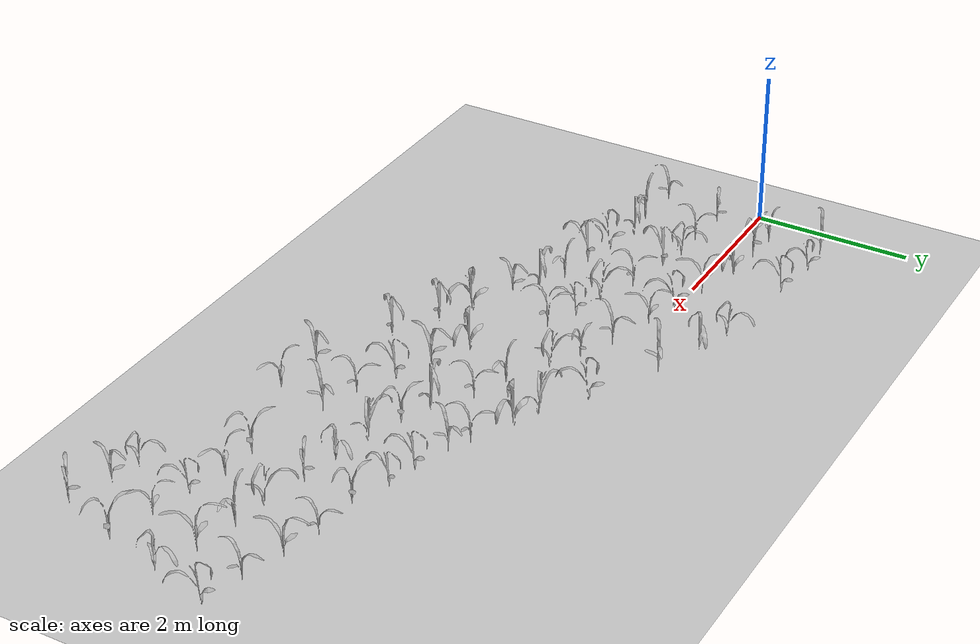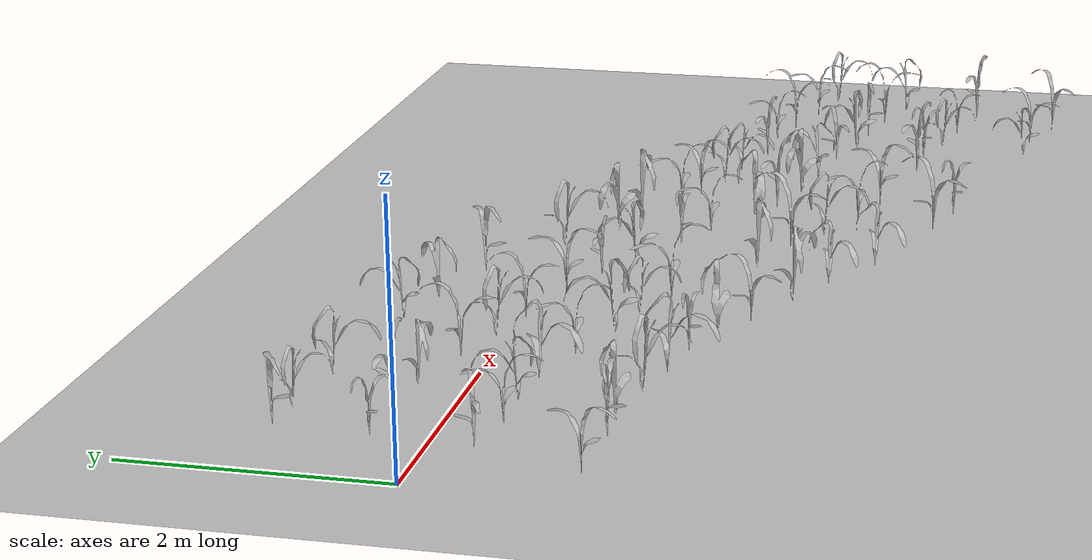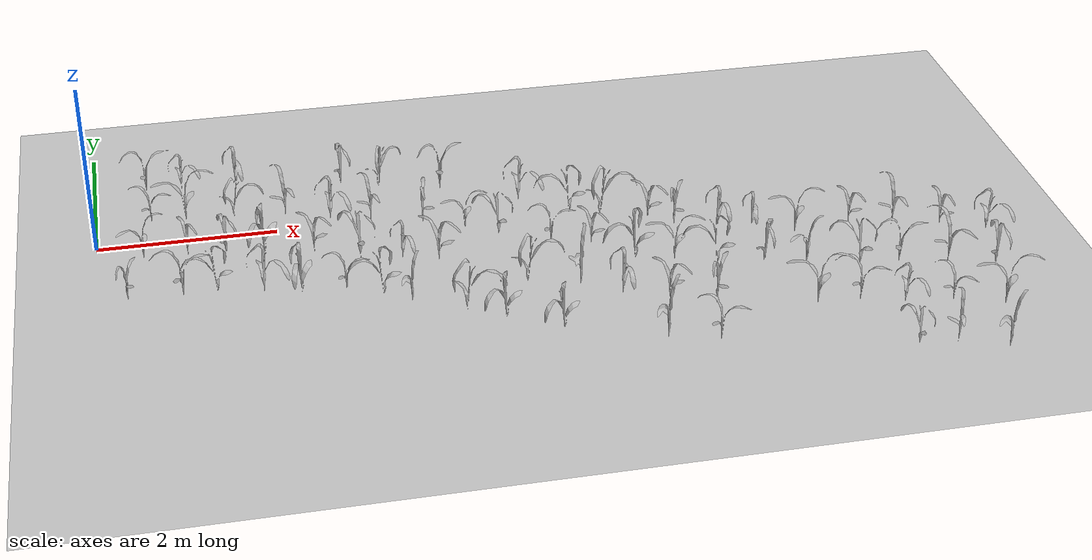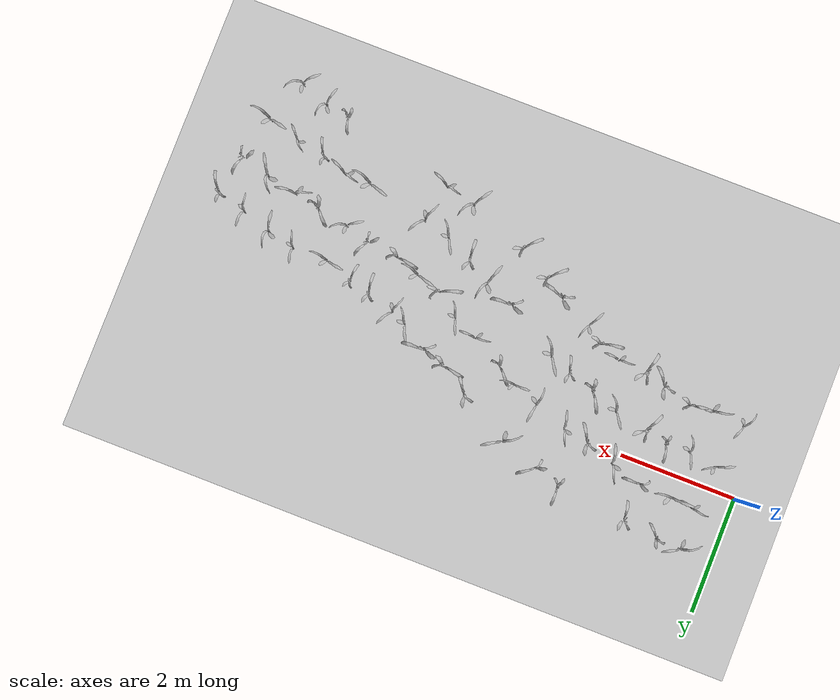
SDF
<sdf version="1.6">
 <world name="default">
  <light name="sun" type="directional">
   <pose>0 0 10 0 -0 0</pose>
   <diffuse>0.8 0.8 0.8 1</diffuse>
   <specular>0.2 0.2 0.2 1</specular>
   <attenuation>
    <range>1000</range>
    <constant>0.9</constant>
    <linear>0.01</linear>
    <quadratic>0.001</quadratic>
   </attenuation>
   <direction>-0.5 0.1 -0.9</direction>
  </light>
  <model name="ground_plane">
   <static>1</static>
   <link name="link">
    <collision name="collision">
     <geometry><plane><normal>0 0 1</normal><size>100 100</size></plane></geometry>
     <surface>
      <contact><collide_bitmask>65535</collide_bitmask></contact>
      <friction><ode><mu>100</mu><mu2>50</mu2></ode></friction>
     </surface>
    </collision>
    <visual name="visual">
     <cast_shadows>0</cast_shadows>
     <geometry><plane><normal>0 0 1</normal><size>100 100</size></plane></geometry>
     <material>
      <script><uri>file://media/materials/scripts/gazebo.material</uri><name>Gazebo/Grey</name></script>
     </material>
    </visual>
   </link>
  </model>
  <gravity>0 0 -9.8</gravity>
  <magnetic_field>6e-06 2.3e-05 -4.2e-05</magnetic_field>
  <atmosphere type="adiabatic"/>
  <physics name="default_physics" default="0" type="ode">
   <max_step_size>0.001</max_step_size>
   <real_time_factor>1</real_time_factor>
   <real_time_update_rate>1000</real_time_update_rate>
  </physics>
  <scene><ambient>0.4 0.4 0.4 1</ambient><background>0.7 0.7 0.7 1</background><shadows>1</shadows></scene>
  <audio><device>default</device></audio>
  <spherical_coordinates>
   <surface_model>EARTH_WGS84</surface_model>
   <latitude_deg>0</latitude_deg>
   <longitude_deg>0</longitude_deg>
   <elevation>0</elevation>
   <heading_deg>0</heading_deg>
  </spherical_coordinates>
  <model name="maize_02_0000">
   <pose>0.6266364575345471 0.39372613624309966 0.05 0 -0 1.9641627684335625</pose>
   <link name="maize_02_0000_link">
    <inertial>
     <mass>5.0</mass>
     <inertia>
      <ixx>0.0033416667</ixx>
      <ixy>0</ixy>
      <ixz>0</ixz>
      <iyy>0.0033416667</iyy>
      <iyz>0</iyz>
      <izz>0.000016666667</izz>
     </inertia>
     <pose>0 0 0.1 0 0 0</pose>
    </inertial>
    <collision name="collision">
     <pose>0 0 0.2 0 -0 0</pose>
     <geometry><box><size>0.02 0.02 0.4</size></box></geometry>
     <surface><friction><ode><mu>10</mu><mu2>10</mu2></ode></friction></surface>
    </collision>
    <visual name="visual">
     <geometry>
      <mesh>
       <uri>model://maize_02/meshes/maize_02.dae</uri>
       <scale>0.5086841816509051 0.5086841816509051 0.5086841816509051</scale>
      </mesh>
     </geometry>
    </visual>
   </link>
  </model>
  <model name="maize_02_0001">
   <pose>0.5962759465924191 1.0790101247407116 0.05 0 -0 2.660585233036896</pose>
   <link name="maize_02_0001_link">
    <inertial>
     <mass>5.0</mass>
     <inertia>
      <ixx>0.0033416667</ixx>
      <ixy>0</ixy>
      <ixz>0</ixz>
      <iyy>0.0033416667</iyy>
      <iyz>0</iyz>
      <izz>0.000016666667</izz>
     </inertia>
     <pose>0 0 0.1 0 0 0</pose>
    </inertial>
    <collision name="collision">
     <pose>0 0 0.2 0 -0 0</pose>
     <geometry><box><size>0.02 0.02 0.4</size></box></geometry>
     <surface><friction><ode><mu>10</mu><mu2>10</mu2></ode></friction></surface>
    </collision>
    <visual name="visual">
     <geometry>
      <mesh>
       <uri>model://maize_02/meshes/maize_02.dae</uri>
       <scale>0.6406825514052783 0.6406825514052783 0.6406825514052783</scale>
      </mesh>
     </geometry>
    </visual>
   </link>
  </model>
  <model name="maize_02_0002">
   <pose>0.5128687947471398 -0.3780994728694755 0.05 0 -0 5.74405830510388</pose>
   <link name="maize_02_0002_link">
    <inertial>
     <mass>5.0</mass>
     <inertia>
      <ixx>0.0033416667</ixx>
      <ixy>0</ixy>
      <ixz>0</ixz>
      <iyy>0.0033416667</iyy>
      <iyz>0</iyz>
      <izz>0.000016666667</izz>
     </inertia>
     <pose>0 0 0.1 0 0 0</pose>
    </inertial>
    <collision name="collision">
     <pose>0 0 0.2 0 -0 0</pose>
     <geometry><box><size>0.02 0.02 0.4</size></box></geometry>
     <surface><friction><ode><mu>10</mu><mu2>10</mu2></ode></friction></surface>
    </collision>
    <visual name="visual">
     <geometry>
      <mesh>
       <uri>model://maize_02/meshes/maize_02.dae</uri>
       <scale>0.5696515739499298 0.5696515739499298 0.5696515739499298</scale>
      </mesh>
     </geometry>
    </visual>
   </link>
  </model>
  <model name="maize_02_0003">
   <pose>0.31845714802949465 -1.1657478187782875 0.05 0 -0 3.3294222100646813</pose>
   <link name="maize_02_0003_link">
    <inertial>
     <mass>5.0</mass>
     <inertia>
      <ixx>0.0033416667</ixx>
      <ixy>0</ixy>
      <ixz>0</ixz>
      <iyy>0.0033416667</iyy>
      <iyz>0</iyz>
      <izz>0.000016666667</izz>
     </inertia>
     <pose>0 0 0.1 0 0 0</pose>
    </inertial>
    <collision name="collision">
     <pose>0 0 0.2 0 -0 0</pose>
     <geometry><box><size>0.02 0.02 0.4</size></box></geometry>
     <surface><friction><ode><mu>10</mu><mu2>10</mu2></ode></friction></surface>
    </collision>
    <visual name="visual">
     <geometry>
      <mesh>
       <uri>model://maize_02/meshes/maize_02.dae</uri>
       <scale>0.5413600755372572 0.5413600755372572 0.5413600755372572</scale>
      </mesh>
     </geometry>
    </visual>
   </link>
  </model>
  <model name="maize_02_0004">
   <pose>1.010929968299112 0.35485476023361967 0.05 0 -0 5.314568562107953</pose>
   <link name="maize_02_0004_link">
    <inertial>
     <mass>5.0</mass>
     <inertia>
      <ixx>0.0033416667</ixx>
      <ixy>0</ixy>
      <ixz>0</ixz>
      <iyy>0.0033416667</iyy>
      <iyz>0</iyz>
      <izz>0.000016666667</izz>
     </inertia>
     <pose>0 0 0.1 0 0 0</pose>
    </inertial>
    <collision name="collision">
     <pose>0 0 0.2 0 -0 0</pose>
     <geometry><box><size>0.02 0.02 0.4</size></box></geometry>
     <surface><friction><ode><mu>10</mu><mu2>10</mu2></ode></friction></surface>
    </collision>
    <visual name="visual">
     <geometry>
      <mesh>
       <uri>model://maize_02/meshes/maize_02.dae</uri>
       <scale>0.6919220891193916 0.6919220891193916 0.6919220891193916</scale>
      </mesh>
     </geometry>
    </visual>
   </link>
  </model>
  <model name="maize_01_0005">
   <pose>0.9939459487335675 1.081394744851532 0.05 0 -0 6.267126563444176</pose>
   <link name="maize_01_0005_link">
    <inertial>
     <mass>5.0</mass>
     <inertia>
      <ixx>0.0033416667</ixx>
      <ixy>0</ixy>
      <ixz>0</ixz>
      <iyy>0.0033416667</iyy>
      <iyz>0</iyz>
      <izz>0.000016666667</izz>
     </inertia>
     <pose>0 0 0.1 0 0 0</pose>
    </inertial>
    <collision name="collision">
     <pose>0 0 0.2 0 -0 0</pose>
     <geometry><box><size>0.02 0.02 0.4</size></box></geometry>
     <surface><friction><ode><mu>10</mu><mu2>10</mu2></ode></friction></surface>
    </collision>
    <visual name="visual">
     <geometry>
      <mesh>
       <uri>model://maize_01/meshes/maize_01.dae</uri>
       <scale>0.5041995030593036 0.5041995030593036 0.5041995030593036</scale>
      </mesh>
     </geometry>
    </visual>
   </link>
  </model>
  <model name="maize_02_0006">
   <pose>0.9931900532488495 -0.4531246310262997 0.05 0 -0 4.064353292946309</pose>
   <link name="maize_02_0006_link">
    <inertial>
     <mass>5.0</mass>
     <inertia>
      <ixx>0.0033416667</ixx>
      <ixy>0</ixy>
      <ixz>0</ixz>
      <iyy>0.0033416667</iyy>
      <iyz>0</iyz>
      <izz>0.000016666667</izz>
     </inertia>
     <pose>0 0 0.1 0 0 0</pose>
    </inertial>
    <collision name="collision">
     <pose>0 0 0.2 0 -0 0</pose>
     <geometry><box><size>0.02 0.02 0.4</size></box></geometry>
     <surface><friction><ode><mu>10</mu><mu2>10</mu2></ode></friction></surface>
    </collision>
    <visual name="visual">
     <geometry>
      <mesh>
       <uri>model://maize_02/meshes/maize_02.dae</uri>
       <scale>0.5553610326463208 0.5553610326463208 0.5553610326463208</scale>
      </mesh>
     </geometry>
    </visual>
   </link>
  </model>
  <model name="maize_02_0007">
   <pose>0.9022254378881605 -1.2091889074268443 0.05 0 -0 2.301816142782291</pose>
   <link name="maize_02_0007_link">
    <inertial>
     <mass>5.0</mass>
     <inertia>
      <ixx>0.0033416667</ixx>
      <ixy>0</ixy>
      <ixz>0</ixz>
      <iyy>0.0033416667</iyy>
      <iyz>0</iyz>
      <izz>0.000016666667</izz>
     </inertia>
     <pose>0 0 0.1 0 0 0</pose>
    </inertial>
    <collision name="collision">
     <pose>0 0 0.2 0 -0 0</pose>
     <geometry><box><size>0.02 0.02 0.4</size></box></geometry>
     <surface><friction><ode><mu>10</mu><mu2>10</mu2></ode></friction></surface>
    </collision>
    <visual name="visual">
     <geometry>
      <mesh>
       <uri>model://maize_02/meshes/maize_02.dae</uri>
       <scale>0.6560324845618973 0.6560324845618973 0.6560324845618973</scale>
      </mesh>
     </geometry>
    </visual>
   </link>
  </model>
  <model name="maize_01_0008">
   <pose>1.5543757841614014 0.32974811669279225 0.05 0 -0 0.7992736679091289</pose>
   <link name="maize_01_0008_link">
    <inertial>
     <mass>5.0</mass>
     <inertia>
      <ixx>0.0033416667</ixx>
      <ixy>0</ixy>
      <ixz>0</ixz>
      <iyy>0.0033416667</iyy>
      <iyz>0</iyz>
      <izz>0.000016666667</izz>
     </inertia>
     <pose>0 0 0.1 0 0 0</pose>
    </inertial>
    <collision name="collision">
     <pose>0 0 0.2 0 -0 0</pose>
     <geometry><box><size>0.02 0.02 0.4</size></box></geometry>
     <surface><friction><ode><mu>10</mu><mu2>10</mu2></ode></friction></surface>
    </collision>
    <visual name="visual">
     <geometry>
      <mesh>
       <uri>model://maize_01/meshes/maize_01.dae</uri>
       <scale>0.5563104025952799 0.5563104025952799 0.5563104025952799</scale>
      </mesh>
     </geometry>
    </visual>
   </link>
  </model>
  <model name="maize_01_0009">
   <pose>1.6142526512537347 0.9980892180156831 0.05 0 -0 5.677408055906511</pose>
   <link name="maize_01_0009_link">
    <inertial>
     <mass>5.0</mass>
     <inertia>
      <ixx>0.0033416667</ixx>
      <ixy>0</ixy>
      <ixz>0</ixz>
      <iyy>0.0033416667</iyy>
      <iyz>0</iyz>
      <izz>0.000016666667</izz>
     </inertia>
     <pose>0 0 0.1 0 0 0</pose>
    </inertial>
    <collision name="collision">
     <pose>0 0 0.2 0 -0 0</pose>
     <geometry><box><size>0.02 0.02 0.4</size></box></geometry>
     <surface><friction><ode><mu>10</mu><mu2>10</mu2></ode></friction></surface>
    </collision>
    <visual name="visual">
     <geometry>
      <mesh>
       <uri>model://maize_01/meshes/maize_01.dae</uri>
       <scale>0.5870345795003608 0.5870345795003608 0.5870345795003608</scale>
      </mesh>
     </geometry>
    </visual>
   </link>
  </model>
  <model name="maize_01_0010">
   <pose>1.4126763547098145 -0.4428748331876621 0.05 0 -0 2.5425948862840824</pose>
   <link name="maize_01_0010_link">
    <inertial>
     <mass>5.0</mass>
     <inertia>
      <ixx>0.0033416667</ixx>
      <ixy>0</ixy>
      <ixz>0</ixz>
      <iyy>0.0033416667</iyy>
      <iyz>0</iyz>
      <izz>0.000016666667</izz>
     </inertia>
     <pose>0 0 0.1 0 0 0</pose>
    </inertial>
    <collision name="collision">
     <pose>0 0 0.2 0 -0 0</pose>
     <geometry><box><size>0.02 0.02 0.4</size></box></geometry>
     <surface><friction><ode><mu>10</mu><mu2>10</mu2></ode></friction></surface>
    </collision>
    <visual name="visual">
     <geometry>
      <mesh>
       <uri>model://maize_01/meshes/maize_01.dae</uri>
       <scale>0.5321163581084744 0.5321163581084744 0.5321163581084744</scale>
      </mesh>
     </geometry>
    </visual>
   </link>
  </model>
  <model name="maize_01_0011">
   <pose>1.2613246954050141 -1.1810825126649775 0.05 0 -0 3.9880871282682717</pose>
   <link name="maize_01_0011_link">
    <inertial>
     <mass>5.0</mass>
     <inertia>
      <ixx>0.0033416667</ixx>
      <ixy>0</ixy>
      <ixz>0</ixz>
      <iyy>0.0033416667</iyy>
      <iyz>0</iyz>
      <izz>0.000016666667</izz>
     </inertia>
     <pose>0 0 0.1 0 0 0</pose>
    </inertial>
    <collision name="collision">
     <pose>0 0 0.2 0 -0 0</pose>
     <geometry><box><size>0.02 0.02 0.4</size></box></geometry>
     <surface><friction><ode><mu>10</mu><mu2>10</mu2></ode></friction></surface>
    </collision>
    <visual name="visual">
     <geometry>
      <mesh>
       <uri>model://maize_01/meshes/maize_01.dae</uri>
       <scale>0.6214562390623211 0.6214562390623211 0.6214562390623211</scale>
      </mesh>
     </geometry>
    </visual>
   </link>
  </model>
  <model name="maize_02_0012">
   <pose>2.117381381137382 0.17774427089105627 0.05 0 -0 0.8896829542763507</pose>
   <link name="maize_02_0012_link">
    <inertial>
     <mass>5.0</mass>
     <inertia>
      <ixx>0.0033416667</ixx>
      <ixy>0</ixy>
      <ixz>0</ixz>
      <iyy>0.0033416667</iyy>
      <iyz>0</iyz>
      <izz>0.000016666667</izz>
     </inertia>
     <pose>0 0 0.1 0 0 0</pose>
    </inertial>
    <collision name="collision">
     <pose>0 0 0.2 0 -0 0</pose>
     <geometry><box><size>0.02 0.02 0.4</size></box></geometry>
     <surface><friction><ode><mu>10</mu><mu2>10</mu2></ode></friction></surface>
    </collision>
    <visual name="visual">
     <geometry>
      <mesh>
       <uri>model://maize_02/meshes/maize_02.dae</uri>
       <scale>0.6501948061595682 0.6501948061595682 0.6501948061595682</scale>
      </mesh>
     </geometry>
    </visual>
   </link>
  </model>
  <model name="maize_01_0013">
   <pose>1.8214492115148906 -0.49392862979805585 0.05 0 -0 5.032388599302817</pose>
   <link name="maize_01_0013_link">
    <inertial>
     <mass>5.0</mass>
     <inertia>
      <ixx>0.0033416667</ixx>
      <ixy>0</ixy>
      <ixz>0</ixz>
      <iyy>0.0033416667</iyy>
      <iyz>0</iyz>
      <izz>0.000016666667</izz>
     </inertia>
     <pose>0 0 0.1 0 0 0</pose>
    </inertial>
    <collision name="collision">
     <pose>0 0 0.2 0 -0 0</pose>
     <geometry><box><size>0.02 0.02 0.4</size></box></geometry>
     <surface><friction><ode><mu>10</mu><mu2>10</mu2></ode></friction></surface>
    </collision>
    <visual name="visual">
     <geometry>
      <mesh>
       <uri>model://maize_01/meshes/maize_01.dae</uri>
       <scale>0.6718502290288646 0.6718502290288646 0.6718502290288646</scale>
      </mesh>
     </geometry>
    </visual>
   </link>
  </model>
  <model name="maize_01_0014">
   <pose>1.7509077911397395 -1.278315929472419 0.05 0 -0 6.197729006710317</pose>
   <link name="maize_01_0014_link">
    <inertial>
     <mass>5.0</mass>
     <inertia>
      <ixx>0.0033416667</ixx>
      <ixy>0</ixy>
      <ixz>0</ixz>
      <iyy>0.0033416667</iyy>
      <iyz>0</iyz>
      <izz>0.000016666667</izz>
     </inertia>
     <pose>0 0 0.1 0 0 0</pose>
    </inertial>
    <collision name="collision">
     <pose>0 0 0.2 0 -0 0</pose>
     <geometry><box><size>0.02 0.02 0.4</size></box></geometry>
     <surface><friction><ode><mu>10</mu><mu2>10</mu2></ode></friction></surface>
    </collision>
    <visual name="visual">
     <geometry>
      <mesh>
       <uri>model://maize_01/meshes/maize_01.dae</uri>
       <scale>0.6485499601028807 0.6485499601028807 0.6485499601028807</scale>
      </mesh>
     </geometry>
    </visual>
   </link>
  </model>
  <model name="maize_01_0015">
   <pose>2.610562871970983 0.04088491732596357 0.05 0 -0 6.052160604748576</pose>
   <link name="maize_01_0015_link">
    <inertial>
     <mass>5.0</mass>
     <inertia>
      <ixx>0.0033416667</ixx>
      <ixy>0</ixy>
      <ixz>0</ixz>
      <iyy>0.0033416667</iyy>
      <iyz>0</iyz>
      <izz>0.000016666667</izz>
     </inertia>
     <pose>0 0 0.1 0 0 0</pose>
    </inertial>
    <collision name="collision">
     <pose>0 0 0.2 0 -0 0</pose>
     <geometry><box><size>0.02 0.02 0.4</size></box></geometry>
     <surface><friction><ode><mu>10</mu><mu2>10</mu2></ode></friction></surface>
    </collision>
    <visual name="visual">
     <geometry>
      <mesh>
       <uri>model://maize_01/meshes/maize_01.dae</uri>
       <scale>0.6244497621583954 0.6244497621583954 0.6244497621583954</scale>
      </mesh>
     </geometry>
    </visual>
   </link>
  </model>
  <model name="maize_01_0016">
   <pose>2.827711473248383 0.8460363309560727 0.05 0 -0 2.37700545942292</pose>
   <link name="maize_01_0016_link">
    <inertial>
     <mass>5.0</mass>
     <inertia>
      <ixx>0.0033416667</ixx>
      <ixy>0</ixy>
      <ixz>0</ixz>
      <iyy>0.0033416667</iyy>
      <iyz>0</iyz>
      <izz>0.000016666667</izz>
     </inertia>
     <pose>0 0 0.1 0 0 0</pose>
    </inertial>
    <collision name="collision">
     <pose>0 0 0.2 0 -0 0</pose>
     <geometry><box><size>0.02 0.02 0.4</size></box></geometry>
     <surface><friction><ode><mu>10</mu><mu2>10</mu2></ode></friction></surface>
    </collision>
    <visual name="visual">
     <geometry>
      <mesh>
       <uri>model://maize_01/meshes/maize_01.dae</uri>
       <scale>0.555690913712643 0.555690913712643 0.555690913712643</scale>
      </mesh>
     </geometry>
    </visual>
   </link>
  </model>
  <model name="maize_02_0017">
   <pose>2.3609275584324414 -0.6368521212228666 0.05 0 -0 4.3213343489436085</pose>
   <link name="maize_02_0017_link">
    <inertial>
     <mass>5.0</mass>
     <inertia>
      <ixx>0.0033416667</ixx>
      <ixy>0</ixy>
      <ixz>0</ixz>
      <iyy>0.0033416667</iyy>
      <iyz>0</iyz>
      <izz>0.000016666667</izz>
     </inertia>
     <pose>0 0 0.1 0 0 0</pose>
    </inertial>
    <collision name="collision">
     <pose>0 0 0.2 0 -0 0</pose>
     <geometry><box><size>0.02 0.02 0.4</size></box></geometry>
     <surface><friction><ode><mu>10</mu><mu2>10</mu2></ode></friction></surface>
    </collision>
    <visual name="visual">
     <geometry>
      <mesh>
       <uri>model://maize_02/meshes/maize_02.dae</uri>
       <scale>0.5812758422849028 0.5812758422849028 0.5812758422849028</scale>
      </mesh>
     </geometry>
    </visual>
   </link>
  </model>
  <model name="maize_01_0018">
   <pose>2.145035071532286 -1.3780438463552462 0.05 0 -0 5.251775204471827</pose>
   <link name="maize_01_0018_link">
    <inertial>
     <mass>5.0</mass>
     <inertia>
      <ixx>0.0033416667</ixx>
      <ixy>0</ixy>
      <ixz>0</ixz>
      <iyy>0.0033416667</iyy>
      <iyz>0</iyz>
      <izz>0.000016666667</izz>
     </inertia>
     <pose>0 0 0.1 0 0 0</pose>
    </inertial>
    <collision name="collision">
     <pose>0 0 0.2 0 -0 0</pose>
     <geometry><box><size>0.02 0.02 0.4</size></box></geometry>
     <surface><friction><ode><mu>10</mu><mu2>10</mu2></ode></friction></surface>
    </collision>
    <visual name="visual">
     <geometry>
      <mesh>
       <uri>model://maize_01/meshes/maize_01.dae</uri>
       <scale>0.6734187363013082 0.6734187363013082 0.6734187363013082</scale>
      </mesh>
     </geometry>
    </visual>
   </link>
  </model>
  <model name="maize_02_0019">
   <pose>3.0561824692400577 -0.07343694835041675 0.05 0 -0 0.8680041697787753</pose>
   <link name="maize_02_0019_link">
    <inertial>
     <mass>5.0</mass>
     <inertia>
      <ixx>0.0033416667</ixx>
      <ixy>0</ixy>
      <ixz>0</ixz>
      <iyy>0.0033416667</iyy>
      <iyz>0</iyz>
      <izz>0.000016666667</izz>
     </inertia>
     <pose>0 0 0.1 0 0 0</pose>
    </inertial>
    <collision name="collision">
     <pose>0 0 0.2 0 -0 0</pose>
     <geometry><box><size>0.02 0.02 0.4</size></box></geometry>
     <surface><friction><ode><mu>10</mu><mu2>10</mu2></ode></friction></surface>
    </collision>
    <visual name="visual">
     <geometry>
      <mesh>
       <uri>model://maize_02/meshes/maize_02.dae</uri>
       <scale>0.5809876807574693 0.5809876807574693 0.5809876807574693</scale>
      </mesh>
     </geometry>
    </visual>
   </link>
  </model>
  <model name="maize_01_0020">
   <pose>3.253096932243729 0.6820665395602563 0.05 0 -0 1.4291629961739294</pose>
   <link name="maize_01_0020_link">
    <inertial>
     <mass>5.0</mass>
     <inertia>
      <ixx>0.0033416667</ixx>
      <ixy>0</ixy>
      <ixz>0</ixz>
      <iyy>0.0033416667</iyy>
      <iyz>0</iyz>
      <izz>0.000016666667</izz>
     </inertia>
     <pose>0 0 0.1 0 0 0</pose>
    </inertial>
    <collision name="collision">
     <pose>0 0 0.2 0 -0 0</pose>
     <geometry><box><size>0.02 0.02 0.4</size></box></geometry>
     <surface><friction><ode><mu>10</mu><mu2>10</mu2></ode></friction></surface>
    </collision>
    <visual name="visual">
     <geometry>
      <mesh>
       <uri>model://maize_01/meshes/maize_01.dae</uri>
       <scale>0.5929236032924424 0.5929236032924424 0.5929236032924424</scale>
      </mesh>
     </geometry>
    </visual>
   </link>
  </model>
  <model name="maize_01_0021">
   <pose>2.8500810738724986 -0.8256093108062299 0.05 0 -0 2.868091574888298</pose>
   <link name="maize_01_0021_link">
    <inertial>
     <mass>5.0</mass>
     <inertia>
      <ixx>0.0033416667</ixx>
      <ixy>0</ixy>
      <ixz>0</ixz>
      <iyy>0.0033416667</iyy>
      <iyz>0</iyz>
      <izz>0.000016666667</izz>
     </inertia>
     <pose>0 0 0.1 0 0 0</pose>
    </inertial>
    <collision name="collision">
     <pose>0 0 0.2 0 -0 0</pose>
     <geometry><box><size>0.02 0.02 0.4</size></box></geometry>
     <surface><friction><ode><mu>10</mu><mu2>10</mu2></ode></friction></surface>
    </collision>
    <visual name="visual">
     <geometry>
      <mesh>
       <uri>model://maize_01/meshes/maize_01.dae</uri>
       <scale>0.6555497364067202 0.6555497364067202 0.6555497364067202</scale>
      </mesh>
     </geometry>
    </visual>
   </link>
  </model>
  <model name="maize_02_0022">
   <pose>2.6196600651793935 -1.446786259412549 0.05 0 -0 2.111339940765336</pose>
   <link name="maize_02_0022_link">
    <inertial>
     <mass>5.0</mass>
     <inertia>
      <ixx>0.0033416667</ixx>
      <ixy>0</ixy>
      <ixz>0</ixz>
      <iyy>0.0033416667</iyy>
      <iyz>0</iyz>
      <izz>0.000016666667</izz>
     </inertia>
     <pose>0 0 0.1 0 0 0</pose>
    </inertial>
    <collision name="collision">
     <pose>0 0 0.2 0 -0 0</pose>
     <geometry><box><size>0.02 0.02 0.4</size></box></geometry>
     <surface><friction><ode><mu>10</mu><mu2>10</mu2></ode></friction></surface>
    </collision>
    <visual name="visual">
     <geometry>
      <mesh>
       <uri>model://maize_02/meshes/maize_02.dae</uri>
       <scale>0.5350570079705032 0.5350570079705032 0.5350570079705032</scale>
      </mesh>
     </geometry>
    </visual>
   </link>
  </model>
  <model name="maize_02_0023">
   <pose>3.628240788240428 -0.25932237432375804 0.05 0 -0 3.5959585147650697</pose>
   <link name="maize_02_0023_link">
    <inertial>
     <mass>5.0</mass>
     <inertia>
      <ixx>0.0033416667</ixx>
      <ixy>0</ixy>
      <ixz>0</ixz>
      <iyy>0.0033416667</iyy>
      <iyz>0</iyz>
      <izz>0.000016666667</izz>
     </inertia>
     <pose>0 0 0.1 0 0 0</pose>
    </inertial>
    <collision name="collision">
     <pose>0 0 0.2 0 -0 0</pose>
     <geometry><box><size>0.02 0.02 0.4</size></box></geometry>
     <surface><friction><ode><mu>10</mu><mu2>10</mu2></ode></friction></surface>
    </collision>
    <visual name="visual">
     <geometry>
      <mesh>
       <uri>model://maize_02/meshes/maize_02.dae</uri>
       <scale>0.6202048061788187 0.6202048061788187 0.6202048061788187</scale>
      </mesh>
     </geometry>
    </visual>
   </link>
  </model>
  <model name="maize_02_0024">
   <pose>3.9411512500950634 0.49162132291938226 0.05 0 -0 2.7278973776733535</pose>
   <link name="maize_02_0024_link">
    <inertial>
     <mass>5.0</mass>
     <inertia>
      <ixx>0.0033416667</ixx>
      <ixy>0</ixy>
      <ixz>0</ixz>
      <iyy>0.0033416667</iyy>
      <iyz>0</iyz>
      <izz>0.000016666667</izz>
     </inertia>
     <pose>0 0 0.1 0 0 0</pose>
    </inertial>
    <collision name="collision">
     <pose>0 0 0.2 0 -0 0</pose>
     <geometry><box><size>0.02 0.02 0.4</size></box></geometry>
     <surface><friction><ode><mu>10</mu><mu2>10</mu2></ode></friction></surface>
    </collision>
    <visual name="visual">
     <geometry>
      <mesh>
       <uri>model://maize_02/meshes/maize_02.dae</uri>
       <scale>0.6937054132654896 0.6937054132654896 0.6937054132654896</scale>
      </mesh>
     </geometry>
    </visual>
   </link>
  </model>
  <model name="maize_01_0025">
   <pose>3.2962788645520087 -0.928187140023274 0.05 0 -0 5.79360503332898</pose>
   <link name="maize_01_0025_link">
    <inertial>
     <mass>5.0</mass>
     <inertia>
      <ixx>0.0033416667</ixx>
      <ixy>0</ixy>
      <ixz>0</ixz>
      <iyy>0.0033416667</iyy>
      <iyz>0</iyz>
      <izz>0.000016666667</izz>
     </inertia>
     <pose>0 0 0.1 0 0 0</pose>
    </inertial>
    <collision name="collision">
     <pose>0 0 0.2 0 -0 0</pose>
     <geometry><box><size>0.02 0.02 0.4</size></box></geometry>
     <surface><friction><ode><mu>10</mu><mu2>10</mu2></ode></friction></surface>
    </collision>
    <visual name="visual">
     <geometry>
      <mesh>
       <uri>model://maize_01/meshes/maize_01.dae</uri>
       <scale>0.5284396797696428 0.5284396797696428 0.5284396797696428</scale>
      </mesh>
     </geometry>
    </visual>
   </link>
  </model>
  <model name="maize_01_0026">
   <pose>2.9973162024497375 -1.5905548633543536 0.05 0 -0 4.078197246147852</pose>
   <link name="maize_01_0026_link">
    <inertial>
     <mass>5.0</mass>
     <inertia>
      <ixx>0.0033416667</ixx>
      <ixy>0</ixy>
      <ixz>0</ixz>
      <iyy>0.0033416667</iyy>
      <iyz>0</iyz>
      <izz>0.000016666667</izz>
     </inertia>
     <pose>0 0 0.1 0 0 0</pose>
    </inertial>
    <collision name="collision">
     <pose>0 0 0.2 0 -0 0</pose>
     <geometry><box><size>0.02 0.02 0.4</size></box></geometry>
     <surface><friction><ode><mu>10</mu><mu2>10</mu2></ode></friction></surface>
    </collision>
    <visual name="visual">
     <geometry>
      <mesh>
       <uri>model://maize_01/meshes/maize_01.dae</uri>
       <scale>0.649500148864992 0.649500148864992 0.649500148864992</scale>
      </mesh>
     </geometry>
    </visual>
   </link>
  </model>
  <model name="maize_02_0027">
   <pose>4.074672588797058 -0.44623534887456334 0.05 0 -0 5.3136015967815915</pose>
   <link name="maize_02_0027_link">
    <inertial>
     <mass>5.0</mass>
     <inertia>
      <ixx>0.0033416667</ixx>
      <ixy>0</ixy>
      <ixz>0</ixz>
      <iyy>0.0033416667</iyy>
      <iyz>0</iyz>
      <izz>0.000016666667</izz>
     </inertia>
     <pose>0 0 0.1 0 0 0</pose>
    </inertial>
    <collision name="collision">
     <pose>0 0 0.2 0 -0 0</pose>
     <geometry><box><size>0.02 0.02 0.4</size></box></geometry>
     <surface><friction><ode><mu>10</mu><mu2>10</mu2></ode></friction></surface>
    </collision>
    <visual name="visual">
     <geometry>
      <mesh>
       <uri>model://maize_02/meshes/maize_02.dae</uri>
       <scale>0.5188962655965342 0.5188962655965342 0.5188962655965342</scale>
      </mesh>
     </geometry>
    </visual>
   </link>
  </model>
  <model name="maize_02_0028">
   <pose>3.676957466873761 -1.103463109708256 0.05 0 -0 4.300579717721141</pose>
   <link name="maize_02_0028_link">
    <inertial>
     <mass>5.0</mass>
     <inertia>
      <ixx>0.0033416667</ixx>
      <ixy>0</ixy>
      <ixz>0</ixz>
      <iyy>0.0033416667</iyy>
      <iyz>0</iyz>
      <izz>0.000016666667</izz>
     </inertia>
     <pose>0 0 0.1 0 0 0</pose>
    </inertial>
    <collision name="collision">
     <pose>0 0 0.2 0 -0 0</pose>
     <geometry><box><size>0.02 0.02 0.4</size></box></geometry>
     <surface><friction><ode><mu>10</mu><mu2>10</mu2></ode></friction></surface>
    </collision>
    <visual name="visual">
     <geometry>
      <mesh>
       <uri>model://maize_02/meshes/maize_02.dae</uri>
       <scale>0.6567580944991641 0.6567580944991641 0.6567580944991641</scale>
      </mesh>
     </geometry>
    </visual>
   </link>
  </model>
  <model name="maize_02_0029">
   <pose>3.2753329141627803 -1.8076560237411745 0.05 0 -0 0.12776244219765875</pose>
   <link name="maize_02_0029_link">
    <inertial>
     <mass>5.0</mass>
     <inertia>
      <ixx>0.0033416667</ixx>
      <ixy>0</ixy>
      <ixz>0</ixz>
      <iyy>0.0033416667</iyy>
      <iyz>0</iyz>
      <izz>0.000016666667</izz>
     </inertia>
     <pose>0 0 0.1 0 0 0</pose>
    </inertial>
    <collision name="collision">
     <pose>0 0 0.2 0 -0 0</pose>
     <geometry><box><size>0.02 0.02 0.4</size></box></geometry>
     <surface><friction><ode><mu>10</mu><mu2>10</mu2></ode></friction></surface>
    </collision>
    <visual name="visual">
     <geometry>
      <mesh>
       <uri>model://maize_02/meshes/maize_02.dae</uri>
       <scale>0.5728051474270807 0.5728051474270807 0.5728051474270807</scale>
      </mesh>
     </geometry>
    </visual>
   </link>
  </model>
  <model name="maize_01_0030">
   <pose>4.421838511337381 -0.658126533851357 0.05 0 -0 3.080604276302289</pose>
   <link name="maize_01_0030_link">
    <inertial>
     <mass>5.0</mass>
     <inertia>
      <ixx>0.0033416667</ixx>
      <ixy>0</ixy>
      <ixz>0</ixz>
      <iyy>0.0033416667</iyy>
      <iyz>0</iyz>
      <izz>0.000016666667</izz>
     </inertia>
     <pose>0 0 0.1 0 0 0</pose>
    </inertial>
    <collision name="collision">
     <pose>0 0 0.2 0 -0 0</pose>
     <geometry><box><size>0.02 0.02 0.4</size></box></geometry>
     <surface><friction><ode><mu>10</mu><mu2>10</mu2></ode></friction></surface>
    </collision>
    <visual name="visual">
     <geometry>
      <mesh>
       <uri>model://maize_01/meshes/maize_01.dae</uri>
       <scale>0.6058283559218649 0.6058283559218649 0.6058283559218649</scale>
      </mesh>
     </geometry>
    </visual>
   </link>
  </model>
  <model name="maize_01_0031">
   <pose>4.7747913944289655 0.028605480432138175 0.05 0 -0 6.114018201514687</pose>
   <link name="maize_01_0031_link">
    <inertial>
     <mass>5.0</mass>
     <inertia>
      <ixx>0.0033416667</ixx>
      <ixy>0</ixy>
      <ixz>0</ixz>
      <iyy>0.0033416667</iyy>
      <iyz>0</iyz>
      <izz>0.000016666667</izz>
     </inertia>
     <pose>0 0 0.1 0 0 0</pose>
    </inertial>
    <collision name="collision">
     <pose>0 0 0.2 0 -0 0</pose>
     <geometry><box><size>0.02 0.02 0.4</size></box></geometry>
     <surface><friction><ode><mu>10</mu><mu2>10</mu2></ode></friction></surface>
    </collision>
    <visual name="visual">
     <geometry>
      <mesh>
       <uri>model://maize_01/meshes/maize_01.dae</uri>
       <scale>0.6418534989219045 0.6418534989219045 0.6418534989219045</scale>
      </mesh>
     </geometry>
    </visual>
   </link>
  </model>
  <model name="maize_01_0032">
   <pose>3.8266407645455143 -2.0542169704420634 0.05 0 -0 0.5064677503961031</pose>
   <link name="maize_01_0032_link">
    <inertial>
     <mass>5.0</mass>
     <inertia>
      <ixx>0.0033416667</ixx>
      <ixy>0</ixy>
      <ixz>0</ixz>
      <iyy>0.0033416667</iyy>
      <iyz>0</iyz>
      <izz>0.000016666667</izz>
     </inertia>
     <pose>0 0 0.1 0 0 0</pose>
    </inertial>
    <collision name="collision">
     <pose>0 0 0.2 0 -0 0</pose>
     <geometry><box><size>0.02 0.02 0.4</size></box></geometry>
     <surface><friction><ode><mu>10</mu><mu2>10</mu2></ode></friction></surface>
    </collision>
    <visual name="visual">
     <geometry>
      <mesh>
       <uri>model://maize_01/meshes/maize_01.dae</uri>
       <scale>0.6841275694167503 0.6841275694167503 0.6841275694167503</scale>
      </mesh>
     </geometry>
    </visual>
   </link>
  </model>
  <model name="maize_02_0033">
   <pose>4.960368465998051 -0.9355059873038714 0.05 0 -0 2.1598457677370666</pose>
   <link name="maize_02_0033_link">
    <inertial>
     <mass>5.0</mass>
     <inertia>
      <ixx>0.0033416667</ixx>
      <ixy>0</ixy>
      <ixz>0</ixz>
      <iyy>0.0033416667</iyy>
      <iyz>0</iyz>
      <izz>0.000016666667</izz>
     </inertia>
     <pose>0 0 0.1 0 0 0</pose>
    </inertial>
    <collision name="collision">
     <pose>0 0 0.2 0 -0 0</pose>
     <geometry><box><size>0.02 0.02 0.4</size></box></geometry>
     <surface><friction><ode><mu>10</mu><mu2>10</mu2></ode></friction></surface>
    </collision>
    <visual name="visual">
     <geometry>
      <mesh>
       <uri>model://maize_02/meshes/maize_02.dae</uri>
       <scale>0.5581011642140988 0.5581011642140988 0.5581011642140988</scale>
      </mesh>
     </geometry>
    </visual>
   </link>
  </model>
  <model name="maize_01_0034">
   <pose>5.299077017650404 -0.3171936034555208 0.05 0 -0 3.7479421571614107</pose>
   <link name="maize_01_0034_link">
    <inertial>
     <mass>5.0</mass>
     <inertia>
      <ixx>0.0033416667</ixx>
      <ixy>0</ixy>
      <ixz>0</ixz>
      <iyy>0.0033416667</iyy>
      <iyz>0</iyz>
      <izz>0.000016666667</izz>
     </inertia>
     <pose>0 0 0.1 0 0 0</pose>
    </inertial>
    <collision name="collision">
     <pose>0 0 0.2 0 -0 0</pose>
     <geometry><box><size>0.02 0.02 0.4</size></box></geometry>
     <surface><friction><ode><mu>10</mu><mu2>10</mu2></ode></friction></surface>
    </collision>
    <visual name="visual">
     <geometry>
      <mesh>
       <uri>model://maize_01/meshes/maize_01.dae</uri>
       <scale>0.661183497575986 0.661183497575986 0.661183497575986</scale>
      </mesh>
     </geometry>
    </visual>
   </link>
  </model>
  <model name="maize_01_0035">
   <pose>4.5571934358591415 -1.655143968629076 0.05 0 -0 0.8561002226769375</pose>
   <link name="maize_01_0035_link">
    <inertial>
     <mass>5.0</mass>
     <inertia>
      <ixx>0.0033416667</ixx>
      <ixy>0</ixy>
      <ixz>0</ixz>
      <iyy>0.0033416667</iyy>
      <iyz>0</iyz>
      <izz>0.000016666667</izz>
     </inertia>
     <pose>0 0 0.1 0 0 0</pose>
    </inertial>
    <collision name="collision">
     <pose>0 0 0.2 0 -0 0</pose>
     <geometry><box><size>0.02 0.02 0.4</size></box></geometry>
     <surface><friction><ode><mu>10</mu><mu2>10</mu2></ode></friction></surface>
    </collision>
    <visual name="visual">
     <geometry>
      <mesh>
       <uri>model://maize_01/meshes/maize_01.dae</uri>
       <scale>0.6620862601144785 0.6620862601144785 0.6620862601144785</scale>
      </mesh>
     </geometry>
    </visual>
   </link>
  </model>
  <model name="maize_01_0036">
   <pose>4.198551510706265 -2.284944472782861 0.05 0 -0 4.681897560401231</pose>
   <link name="maize_01_0036_link">
    <inertial>
     <mass>5.0</mass>
     <inertia>
      <ixx>0.0033416667</ixx>
      <ixy>0</ixy>
      <ixz>0</ixz>
      <iyy>0.0033416667</iyy>
      <iyz>0</iyz>
      <izz>0.000016666667</izz>
     </inertia>
     <pose>0 0 0.1 0 0 0</pose>
    </inertial>
    <collision name="collision">
     <pose>0 0 0.2 0 -0 0</pose>
     <geometry><box><size>0.02 0.02 0.4</size></box></geometry>
     <surface><friction><ode><mu>10</mu><mu2>10</mu2></ode></friction></surface>
    </collision>
    <visual name="visual">
     <geometry>
      <mesh>
       <uri>model://maize_01/meshes/maize_01.dae</uri>
       <scale>0.6173646528607816 0.6173646528607816 0.6173646528607816</scale>
      </mesh>
     </geometry>
    </visual>
   </link>
  </model>
  <model name="maize_02_0037">
   <pose>5.380826796983916 -1.1121444295785388 0.05 0 -0 4.131736003612845</pose>
   <link name="maize_02_0037_link">
    <inertial>
     <mass>5.0</mass>
     <inertia>
      <ixx>0.0033416667</ixx>
      <ixy>0</ixy>
      <ixz>0</ixz>
      <iyy>0.0033416667</iyy>
      <iyz>0</iyz>
      <izz>0.000016666667</izz>
     </inertia>
     <pose>0 0 0.1 0 0 0</pose>
    </inertial>
    <collision name="collision">
     <pose>0 0 0.2 0 -0 0</pose>
     <geometry><box><size>0.02 0.02 0.4</size></box></geometry>
     <surface><friction><ode><mu>10</mu><mu2>10</mu2></ode></friction></surface>
    </collision>
    <visual name="visual">
     <geometry>
      <mesh>
       <uri>model://maize_02/meshes/maize_02.dae</uri>
       <scale>0.5576618371659392 0.5576618371659392 0.5576618371659392</scale>
      </mesh>
     </geometry>
    </visual>
   </link>
  </model>
  <model name="maize_01_0038">
   <pose>5.636869973974431 -0.4515647427213715 0.05 0 -0 0.8495256848192918</pose>
   <link name="maize_01_0038_link">
    <inertial>
     <mass>5.0</mass>
     <inertia>
      <ixx>0.0033416667</ixx>
      <ixy>0</ixy>
      <ixz>0</ixz>
      <iyy>0.0033416667</iyy>
      <iyz>0</iyz>
      <izz>0.000016666667</izz>
     </inertia>
     <pose>0 0 0.1 0 0 0</pose>
    </inertial>
    <collision name="collision">
     <pose>0 0 0.2 0 -0 0</pose>
     <geometry><box><size>0.02 0.02 0.4</size></box></geometry>
     <surface><friction><ode><mu>10</mu><mu2>10</mu2></ode></friction></surface>
    </collision>
    <visual name="visual">
     <geometry>
      <mesh>
       <uri>model://maize_01/meshes/maize_01.dae</uri>
       <scale>0.6989401438620291 0.6989401438620291 0.6989401438620291</scale>
      </mesh>
     </geometry>
    </visual>
   </link>
  </model>
  <model name="maize_02_0039">
   <pose>5.094399492638785 -1.8508619873585384 0.05 0 -0 0.24570918794548977</pose>
   <link name="maize_02_0039_link">
    <inertial>
     <mass>5.0</mass>
     <inertia>
      <ixx>0.0033416667</ixx>
      <ixy>0</ixy>
      <ixz>0</ixz>
      <iyy>0.0033416667</iyy>
      <iyz>0</iyz>
      <izz>0.000016666667</izz>
     </inertia>
     <pose>0 0 0.1 0 0 0</pose>
    </inertial>
    <collision name="collision">
     <pose>0 0 0.2 0 -0 0</pose>
     <geometry><box><size>0.02 0.02 0.4</size></box></geometry>
     <surface><friction><ode><mu>10</mu><mu2>10</mu2></ode></friction></surface>
    </collision>
    <visual name="visual">
     <geometry>
      <mesh>
       <uri>model://maize_02/meshes/maize_02.dae</uri>
       <scale>0.6969056075315362 0.6969056075315362 0.6969056075315362</scale>
      </mesh>
     </geometry>
    </visual>
   </link>
  </model>
  <model name="maize_01_0040">
   <pose>4.751342506149417 -2.5979396704832056 0.05 0 -0 4.720329252662079</pose>
   <link name="maize_01_0040_link">
    <inertial>
     <mass>5.0</mass>
     <inertia>
      <ixx>0.0033416667</ixx>
      <ixy>0</ixy>
      <ixz>0</ixz>
      <iyy>0.0033416667</iyy>
      <iyz>0</iyz>
      <izz>0.000016666667</izz>
     </inertia>
     <pose>0 0 0.1 0 0 0</pose>
    </inertial>
    <collision name="collision">
     <pose>0 0 0.2 0 -0 0</pose>
     <geometry><box><size>0.02 0.02 0.4</size></box></geometry>
     <surface><friction><ode><mu>10</mu><mu2>10</mu2></ode></friction></surface>
    </collision>
    <visual name="visual">
     <geometry>
      <mesh>
       <uri>model://maize_01/meshes/maize_01.dae</uri>
       <scale>0.613702115524717 0.613702115524717 0.613702115524717</scale>
      </mesh>
     </geometry>
    </visual>
   </link>
  </model>
  <model name="maize_01_0041">
   <pose>5.801728931763476 -1.4219378858371343 0.05 0 -0 4.255659404669304</pose>
   <link name="maize_01_0041_link">
    <inertial>
     <mass>5.0</mass>
     <inertia>
      <ixx>0.0033416667</ixx>
      <ixy>0</ixy>
      <ixz>0</ixz>
      <iyy>0.0033416667</iyy>
      <iyz>0</iyz>
      <izz>0.000016666667</izz>
     </inertia>
     <pose>0 0 0.1 0 0 0</pose>
    </inertial>
    <collision name="collision">
     <pose>0 0 0.2 0 -0 0</pose>
     <geometry><box><size>0.02 0.02 0.4</size></box></geometry>
     <surface><friction><ode><mu>10</mu><mu2>10</mu2></ode></friction></surface>
    </collision>
    <visual name="visual">
     <geometry>
      <mesh>
       <uri>model://maize_01/meshes/maize_01.dae</uri>
       <scale>0.6919242030783556 0.6919242030783556 0.6919242030783556</scale>
      </mesh>
     </geometry>
    </visual>
   </link>
  </model>
  <model name="maize_02_0042">
   <pose>6.123002035650348 -0.7153670293230351 0.05 0 -0 4.216375102309107</pose>
   <link name="maize_02_0042_link">
    <inertial>
     <mass>5.0</mass>
     <inertia>
      <ixx>0.0033416667</ixx>
      <ixy>0</ixy>
      <ixz>0</ixz>
      <iyy>0.0033416667</iyy>
      <iyz>0</iyz>
      <izz>0.000016666667</izz>
     </inertia>
     <pose>0 0 0.1 0 0 0</pose>
    </inertial>
    <collision name="collision">
     <pose>0 0 0.2 0 -0 0</pose>
     <geometry><box><size>0.02 0.02 0.4</size></box></geometry>
     <surface><friction><ode><mu>10</mu><mu2>10</mu2></ode></friction></surface>
    </collision>
    <visual name="visual">
     <geometry>
      <mesh>
       <uri>model://maize_02/meshes/maize_02.dae</uri>
       <scale>0.5916385500496594 0.5916385500496594 0.5916385500496594</scale>
      </mesh>
     </geometry>
    </visual>
   </link>
  </model>
  <model name="maize_01_0043">
   <pose>5.503921426295233 -2.078516221017225 0.05 0 -0 5.561816187318802</pose>
   <link name="maize_01_0043_link">
    <inertial>
     <mass>5.0</mass>
     <inertia>
      <ixx>0.0033416667</ixx>
      <ixy>0</ixy>
      <ixz>0</ixz>
      <iyy>0.0033416667</iyy>
      <iyz>0</iyz>
      <izz>0.000016666667</izz>
     </inertia>
     <pose>0 0 0.1 0 0 0</pose>
    </inertial>
    <collision name="collision">
     <pose>0 0 0.2 0 -0 0</pose>
     <geometry><box><size>0.02 0.02 0.4</size></box></geometry>
     <surface><friction><ode><mu>10</mu><mu2>10</mu2></ode></friction></surface>
    </collision>
    <visual name="visual">
     <geometry>
      <mesh>
       <uri>model://maize_01/meshes/maize_01.dae</uri>
       <scale>0.6191261338257424 0.6191261338257424 0.6191261338257424</scale>
      </mesh>
     </geometry>
    </visual>
   </link>
  </model>
  <model name="maize_02_0044">
   <pose>6.210458776372682 -1.560764899580351 0.05 0 -0 5.035069638224472</pose>
   <link name="maize_02_0044_link">
    <inertial>
     <mass>5.0</mass>
     <inertia>
      <ixx>0.0033416667</ixx>
      <ixy>0</ixy>
      <ixz>0</ixz>
      <iyy>0.0033416667</iyy>
      <iyz>0</iyz>
      <izz>0.000016666667</izz>
     </inertia>
     <pose>0 0 0.1 0 0 0</pose>
    </inertial>
    <collision name="collision">
     <pose>0 0 0.2 0 -0 0</pose>
     <geometry><box><size>0.02 0.02 0.4</size></box></geometry>
     <surface><friction><ode><mu>10</mu><mu2>10</mu2></ode></friction></surface>
    </collision>
    <visual name="visual">
     <geometry>
      <mesh>
       <uri>model://maize_02/meshes/maize_02.dae</uri>
       <scale>0.6353333783281057 0.6353333783281057 0.6353333783281057</scale>
      </mesh>
     </geometry>
    </visual>
   </link>
  </model>
  <model name="maize_02_0045">
   <pose>6.397982372111667 -0.8395475908505885 0.05 0 -0 3.256998167592604</pose>
   <link name="maize_02_0045_link">
    <inertial>
     <mass>5.0</mass>
     <inertia>
      <ixx>0.0033416667</ixx>
      <ixy>0</ixy>
      <ixz>0</ixz>
      <iyy>0.0033416667</iyy>
      <iyz>0</iyz>
      <izz>0.000016666667</izz>
     </inertia>
     <pose>0 0 0.1 0 0 0</pose>
    </inertial>
    <collision name="collision">
     <pose>0 0 0.2 0 -0 0</pose>
     <geometry><box><size>0.02 0.02 0.4</size></box></geometry>
     <surface><friction><ode><mu>10</mu><mu2>10</mu2></ode></friction></surface>
    </collision>
    <visual name="visual">
     <geometry>
      <mesh>
       <uri>model://maize_02/meshes/maize_02.dae</uri>
       <scale>0.604300763019085 0.604300763019085 0.604300763019085</scale>
      </mesh>
     </geometry>
    </visual>
   </link>
  </model>
  <model name="maize_02_0046">
   <pose>5.95832853603753 -2.3156317412115106 0.05 0 -0 4.245756654750301</pose>
   <link name="maize_02_0046_link">
    <inertial>
     <mass>5.0</mass>
     <inertia>
      <ixx>0.0033416667</ixx>
      <ixy>0</ixy>
      <ixz>0</ixz>
      <iyy>0.0033416667</iyy>
      <iyz>0</iyz>
      <izz>0.000016666667</izz>
     </inertia>
     <pose>0 0 0.1 0 0 0</pose>
    </inertial>
    <collision name="collision">
     <pose>0 0 0.2 0 -0 0</pose>
     <geometry><box><size>0.02 0.02 0.4</size></box></geometry>
     <surface><friction><ode><mu>10</mu><mu2>10</mu2></ode></friction></surface>
    </collision>
    <visual name="visual">
     <geometry>
      <mesh>
       <uri>model://maize_02/meshes/maize_02.dae</uri>
       <scale>0.5740207718928513 0.5740207718928513 0.5740207718928513</scale>
      </mesh>
     </geometry>
    </visual>
   </link>
  </model>
  <model name="maize_02_0047">
   <pose>5.767986204778223 -2.9865198082212308 0.05 0 -0 6.277337239589561</pose>
   <link name="maize_02_0047_link">
    <inertial>
     <mass>5.0</mass>
     <inertia>
      <ixx>0.0033416667</ixx>
      <ixy>0</ixy>
      <ixz>0</ixz>
      <iyy>0.0033416667</iyy>
      <iyz>0</iyz>
      <izz>0.000016666667</izz>
     </inertia>
     <pose>0 0 0.1 0 0 0</pose>
    </inertial>
    <collision name="collision">
     <pose>0 0 0.2 0 -0 0</pose>
     <geometry><box><size>0.02 0.02 0.4</size></box></geometry>
     <surface><friction><ode><mu>10</mu><mu2>10</mu2></ode></friction></surface>
    </collision>
    <visual name="visual">
     <geometry>
      <mesh>
       <uri>model://maize_02/meshes/maize_02.dae</uri>
       <scale>0.6906433935064686 0.6906433935064686 0.6906433935064686</scale>
      </mesh>
     </geometry>
    </visual>
   </link>
  </model>
  <model name="maize_01_0048">
   <pose>6.649586963596775 -1.7139959033057348 0.05 0 -0 3.755744642376578</pose>
   <link name="maize_01_0048_link">
    <inertial>
     <mass>5.0</mass>
     <inertia>
      <ixx>0.0033416667</ixx>
      <ixy>0</ixy>
      <ixz>0</ixz>
      <iyy>0.0033416667</iyy>
      <iyz>0</iyz>
      <izz>0.000016666667</izz>
     </inertia>
     <pose>0 0 0.1 0 0 0</pose>
    </inertial>
    <collision name="collision">
     <pose>0 0 0.2 0 -0 0</pose>
     <geometry><box><size>0.02 0.02 0.4</size></box></geometry>
     <surface><friction><ode><mu>10</mu><mu2>10</mu2></ode></friction></surface>
    </collision>
    <visual name="visual">
     <geometry>
      <mesh>
       <uri>model://maize_01/meshes/maize_01.dae</uri>
       <scale>0.6616736977128865 0.6616736977128865 0.6616736977128865</scale>
      </mesh>
     </geometry>
    </visual>
   </link>
  </model>
  <model name="maize_01_0049">
   <pose>6.863327963307856 -0.9797606673729811 0.05 0 -0 5.603196610547064</pose>
   <link name="maize_01_0049_link">
    <inertial>
     <mass>5.0</mass>
     <inertia>
      <ixx>0.0033416667</ixx>
      <ixy>0</ixy>
      <ixz>0</ixz>
      <iyy>0.0033416667</iyy>
      <iyz>0</iyz>
      <izz>0.000016666667</izz>
     </inertia>
     <pose>0 0 0.1 0 0 0</pose>
    </inertial>
    <collision name="collision">
     <pose>0 0 0.2 0 -0 0</pose>
     <geometry><box><size>0.02 0.02 0.4</size></box></geometry>
     <surface><friction><ode><mu>10</mu><mu2>10</mu2></ode></friction></surface>
    </collision>
    <visual name="visual">
     <geometry>
      <mesh>
       <uri>model://maize_01/meshes/maize_01.dae</uri>
       <scale>0.5811860311920897 0.5811860311920897 0.5811860311920897</scale>
      </mesh>
     </geometry>
    </visual>
   </link>
  </model>
  <model name="maize_02_0050">
   <pose>6.438861286626614 -2.457105299129998 0.05 0 -0 3.1984705406813494</pose>
   <link name="maize_02_0050_link">
    <inertial>
     <mass>5.0</mass>
     <inertia>
      <ixx>0.0033416667</ixx>
      <ixy>0</ixy>
      <ixz>0</ixz>
      <iyy>0.0033416667</iyy>
      <iyz>0</iyz>
      <izz>0.000016666667</izz>
     </inertia>
     <pose>0 0 0.1 0 0 0</pose>
    </inertial>
    <collision name="collision">
     <pose>0 0 0.2 0 -0 0</pose>
     <geometry><box><size>0.02 0.02 0.4</size></box></geometry>
     <surface><friction><ode><mu>10</mu><mu2>10</mu2></ode></friction></surface>
    </collision>
    <visual name="visual">
     <geometry>
      <mesh>
       <uri>model://maize_02/meshes/maize_02.dae</uri>
       <scale>0.6467942954645587 0.6467942954645587 0.6467942954645587</scale>
      </mesh>
     </geometry>
    </visual>
   </link>
  </model>
  <model name="maize_02_0051">
   <pose>6.298108858958803 -3.1201019149095592 0.05 0 -0 1.7803633762852777</pose>
   <link name="maize_02_0051_link">
    <inertial>
     <mass>5.0</mass>
     <inertia>
      <ixx>0.0033416667</ixx>
      <ixy>0</ixy>
      <ixz>0</ixz>
      <iyy>0.0033416667</iyy>
      <iyz>0</iyz>
      <izz>0.000016666667</izz>
     </inertia>
     <pose>0 0 0.1 0 0 0</pose>
    </inertial>
    <collision name="collision">
     <pose>0 0 0.2 0 -0 0</pose>
     <geometry><box><size>0.02 0.02 0.4</size></box></geometry>
     <surface><friction><ode><mu>10</mu><mu2>10</mu2></ode></friction></surface>
    </collision>
    <visual name="visual">
     <geometry>
      <mesh>
       <uri>model://maize_02/meshes/maize_02.dae</uri>
       <scale>0.5776375116548905 0.5776375116548905 0.5776375116548905</scale>
      </mesh>
     </geometry>
    </visual>
   </link>
  </model>
  <model name="maize_01_0052">
   <pose>7.17118140253864 -1.7989121086785484 0.05 0 -0 1.9193315468450178</pose>
   <link name="maize_01_0052_link">
    <inertial>
     <mass>5.0</mass>
     <inertia>
      <ixx>0.0033416667</ixx>
      <ixy>0</ixy>
      <ixz>0</ixz>
      <iyy>0.0033416667</iyy>
      <iyz>0</iyz>
      <izz>0.000016666667</izz>
     </inertia>
     <pose>0 0 0.1 0 0 0</pose>
    </inertial>
    <collision name="collision">
     <pose>0 0 0.2 0 -0 0</pose>
     <geometry><box><size>0.02 0.02 0.4</size></box></geometry>
     <surface><friction><ode><mu>10</mu><mu2>10</mu2></ode></friction></surface>
    </collision>
    <visual name="visual">
     <geometry>
      <mesh>
       <uri>model://maize_01/meshes/maize_01.dae</uri>
       <scale>0.5720714556326781 0.5720714556326781 0.5720714556326781</scale>
      </mesh>
     </geometry>
    </visual>
   </link>
  </model>
  <model name="maize_01_0053">
   <pose>7.234087771317568 -1.070650363741629 0.05 0 -0 5.360261698219691</pose>
   <link name="maize_01_0053_link">
    <inertial>
     <mass>5.0</mass>
     <inertia>
      <ixx>0.0033416667</ixx>
      <ixy>0</ixy>
      <ixz>0</ixz>
      <iyy>0.0033416667</iyy>
      <iyz>0</iyz>
      <izz>0.000016666667</izz>
     </inertia>
     <pose>0 0 0.1 0 0 0</pose>
    </inertial>
    <collision name="collision">
     <pose>0 0 0.2 0 -0 0</pose>
     <geometry><box><size>0.02 0.02 0.4</size></box></geometry>
     <surface><friction><ode><mu>10</mu><mu2>10</mu2></ode></friction></surface>
    </collision>
    <visual name="visual">
     <geometry>
      <mesh>
       <uri>model://maize_01/meshes/maize_01.dae</uri>
       <scale>0.5070694709388557 0.5070694709388557 0.5070694709388557</scale>
      </mesh>
     </geometry>
    </visual>
   </link>
  </model>
  <model name="maize_02_0054">
   <pose>7.610075070794979 -1.9095222483055125 0.05 0 -0 5.853891303534344</pose>
   <link name="maize_02_0054_link">
    <inertial>
     <mass>5.0</mass>
     <inertia>
      <ixx>0.0033416667</ixx>
      <ixy>0</ixy>
      <ixz>0</ixz>
      <iyy>0.0033416667</iyy>
      <iyz>0</iyz>
      <izz>0.000016666667</izz>
     </inertia>
     <pose>0 0 0.1 0 0 0</pose>
    </inertial>
    <collision name="collision">
     <pose>0 0 0.2 0 -0 0</pose>
     <geometry><box><size>0.02 0.02 0.4</size></box></geometry>
     <surface><friction><ode><mu>10</mu><mu2>10</mu2></ode></friction></surface>
    </collision>
    <visual name="visual">
     <geometry>
      <mesh>
       <uri>model://maize_02/meshes/maize_02.dae</uri>
       <scale>0.5761831144545032 0.5761831144545032 0.5761831144545032</scale>
      </mesh>
     </geometry>
    </visual>
   </link>
  </model>
  <model name="maize_02_0055">
   <pose>7.692980484560454 -1.2409872856509792 0.05 0 -0 5.1338045619563815</pose>
   <link name="maize_02_0055_link">
    <inertial>
     <mass>5.0</mass>
     <inertia>
      <ixx>0.0033416667</ixx>
      <ixy>0</ixy>
      <ixz>0</ixz>
      <iyy>0.0033416667</iyy>
      <iyz>0</iyz>
      <izz>0.000016666667</izz>
     </inertia>
     <pose>0 0 0.1 0 0 0</pose>
    </inertial>
    <collision name="collision">
     <pose>0 0 0.2 0 -0 0</pose>
     <geometry><box><size>0.02 0.02 0.4</size></box></geometry>
     <surface><friction><ode><mu>10</mu><mu2>10</mu2></ode></friction></surface>
    </collision>
    <visual name="visual">
     <geometry>
      <mesh>
       <uri>model://maize_02/meshes/maize_02.dae</uri>
       <scale>0.6120319577522696 0.6120319577522696 0.6120319577522696</scale>
      </mesh>
     </geometry>
    </visual>
   </link>
  </model>
  <model name="maize_02_0056">
   <pose>7.48302492159469 -2.6844494783002095 0.05 0 -0 5.003051203613753</pose>
   <link name="maize_02_0056_link">
    <inertial>
     <mass>5.0</mass>
     <inertia>
      <ixx>0.0033416667</ixx>
      <ixy>0</ixy>
      <ixz>0</ixz>
      <iyy>0.0033416667</iyy>
      <iyz>0</iyz>
      <izz>0.000016666667</izz>
     </inertia>
     <pose>0 0 0.1 0 0 0</pose>
    </inertial>
    <collision name="collision">
     <pose>0 0 0.2 0 -0 0</pose>
     <geometry><box><size>0.02 0.02 0.4</size></box></geometry>
     <surface><friction><ode><mu>10</mu><mu2>10</mu2></ode></friction></surface>
    </collision>
    <visual name="visual">
     <geometry>
      <mesh>
       <uri>model://maize_02/meshes/maize_02.dae</uri>
       <scale>0.6939565961798845 0.6939565961798845 0.6939565961798845</scale>
      </mesh>
     </geometry>
    </visual>
   </link>
  </model>
  <model name="maize_01_0057">
   <pose>8.179087219703533 -2.032215731315807 0.05 0 -0 3.1191036764182445</pose>
   <link name="maize_01_0057_link">
    <inertial>
     <mass>5.0</mass>
     <inertia>
      <ixx>0.0033416667</ixx>
      <ixy>0</ixy>
      <ixz>0</ixz>
      <iyy>0.0033416667</iyy>
      <iyz>0</iyz>
      <izz>0.000016666667</izz>
     </inertia>
     <pose>0 0 0.1 0 0 0</pose>
    </inertial>
    <collision name="collision">
     <pose>0 0 0.2 0 -0 0</pose>
     <geometry><box><size>0.02 0.02 0.4</size></box></geometry>
     <surface><friction><ode><mu>10</mu><mu2>10</mu2></ode></friction></surface>
    </collision>
    <visual name="visual">
     <geometry>
      <mesh>
       <uri>model://maize_01/meshes/maize_01.dae</uri>
       <scale>0.6320471348074791 0.6320471348074791 0.6320471348074791</scale>
      </mesh>
     </geometry>
    </visual>
   </link>
  </model>
  <model name="maize_02_0058">
   <pose>8.318405709210207 -1.2400516035745033 0.05 0 -0 3.9974566228724773</pose>
   <link name="maize_02_0058_link">
    <inertial>
     <mass>5.0</mass>
     <inertia>
      <ixx>0.0033416667</ixx>
      <ixy>0</ixy>
      <ixz>0</ixz>
      <iyy>0.0033416667</iyy>
      <iyz>0</iyz>
      <izz>0.000016666667</izz>
     </inertia>
     <pose>0 0 0.1 0 0 0</pose>
    </inertial>
    <collision name="collision">
     <pose>0 0 0.2 0 -0 0</pose>
     <geometry><box><size>0.02 0.02 0.4</size></box></geometry>
     <surface><friction><ode><mu>10</mu><mu2>10</mu2></ode></friction></surface>
    </collision>
    <visual name="visual">
     <geometry>
      <mesh>
       <uri>model://maize_02/meshes/maize_02.dae</uri>
       <scale>0.537285136365032 0.537285136365032 0.537285136365032</scale>
      </mesh>
     </geometry>
    </visual>
   </link>
  </model>
  <model name="maize_02_0059">
   <pose>7.950962744307331 -2.704367071509 0.05 0 -0 1.7660979900803653</pose>
   <link name="maize_02_0059_link">
    <inertial>
     <mass>5.0</mass>
     <inertia>
      <ixx>0.0033416667</ixx>
      <ixy>0</ixy>
      <ixz>0</ixz>
      <iyy>0.0033416667</iyy>
      <iyz>0</iyz>
      <izz>0.000016666667</izz>
     </inertia>
     <pose>0 0 0.1 0 0 0</pose>
    </inertial>
    <collision name="collision">
     <pose>0 0 0.2 0 -0 0</pose>
     <geometry><box><size>0.02 0.02 0.4</size></box></geometry>
     <surface><friction><ode><mu>10</mu><mu2>10</mu2></ode></friction></surface>
    </collision>
    <visual name="visual">
     <geometry>
      <mesh>
       <uri>model://maize_02/meshes/maize_02.dae</uri>
       <scale>0.5849481296283322 0.5849481296283322 0.5849481296283322</scale>
      </mesh>
     </geometry>
    </visual>
   </link>
  </model>
  <model name="maize_02_0060">
   <pose>8.601920946539888 -2.1021150568137252 0.05 0 -0 2.328476074341754</pose>
   <link name="maize_02_0060_link">
    <inertial>
     <mass>5.0</mass>
     <inertia>
      <ixx>0.0033416667</ixx>
      <ixy>0</ixy>
      <ixz>0</ixz>
      <iyy>0.0033416667</iyy>
      <iyz>0</iyz>
      <izz>0.000016666667</izz>
     </inertia>
     <pose>0 0 0.1 0 0 0</pose>
    </inertial>
    <collision name="collision">
     <pose>0 0 0.2 0 -0 0</pose>
     <geometry><box><size>0.02 0.02 0.4</size></box></geometry>
     <surface><friction><ode><mu>10</mu><mu2>10</mu2></ode></friction></surface>
    </collision>
    <visual name="visual">
     <geometry>
      <mesh>
       <uri>model://maize_02/meshes/maize_02.dae</uri>
       <scale>0.6399658166035169 0.6399658166035169 0.6399658166035169</scale>
      </mesh>
     </geometry>
    </visual>
   </link>
  </model>
  <model name="maize_02_0061">
   <pose>8.790644129741503 -1.354850356359707 0.05 0 -0 0.7179212252596441</pose>
   <link name="maize_02_0061_link">
    <inertial>
     <mass>5.0</mass>
     <inertia>
      <ixx>0.0033416667</ixx>
      <ixy>0</ixy>
      <ixz>0</ixz>
      <iyy>0.0033416667</iyy>
      <iyz>0</iyz>
      <izz>0.000016666667</izz>
     </inertia>
     <pose>0 0 0.1 0 0 0</pose>
    </inertial>
    <collision name="collision">
     <pose>0 0 0.2 0 -0 0</pose>
     <geometry><box><size>0.02 0.02 0.4</size></box></geometry>
     <surface><friction><ode><mu>10</mu><mu2>10</mu2></ode></friction></surface>
    </collision>
    <visual name="visual">
     <geometry>
      <mesh>
       <uri>model://maize_02/meshes/maize_02.dae</uri>
       <scale>0.6422198931139468 0.6422198931139468 0.6422198931139468</scale>
      </mesh>
     </geometry>
    </visual>
   </link>
  </model>
  <model name="maize_01_0062">
   <pose>8.39938005604684 -2.8481918893441773 0.05 0 -0 5.924262318056059</pose>
   <link name="maize_01_0062_link">
    <inertial>
     <mass>5.0</mass>
     <inertia>
      <ixx>0.0033416667</ixx>
      <ixy>0</ixy>
      <ixz>0</ixz>
      <iyy>0.0033416667</iyy>
      <iyz>0</iyz>
      <izz>0.000016666667</izz>
     </inertia>
     <pose>0 0 0.1 0 0 0</pose>
    </inertial>
    <collision name="collision">
     <pose>0 0 0.2 0 -0 0</pose>
     <geometry><box><size>0.02 0.02 0.4</size></box></geometry>
     <surface><friction><ode><mu>10</mu><mu2>10</mu2></ode></friction></surface>
    </collision>
    <visual name="visual">
     <geometry>
      <mesh>
       <uri>model://maize_01/meshes/maize_01.dae</uri>
       <scale>0.5311446698429 0.5311446698429 0.5311446698429</scale>
      </mesh>
     </geometry>
    </visual>
   </link>
  </model>
  <model name="maize_01_0063">
   <pose>8.263704319010111 -3.6234885715072096 0.05 0 -0 2.703705160575316</pose>
   <link name="maize_01_0063_link">
    <inertial>
     <mass>5.0</mass>
     <inertia>
      <ixx>0.0033416667</ixx>
      <ixy>0</ixy>
      <ixz>0</ixz>
      <iyy>0.0033416667</iyy>
      <iyz>0</iyz>
      <izz>0.000016666667</izz>
     </inertia>
     <pose>0 0 0.1 0 0 0</pose>
    </inertial>
    <collision name="collision">
     <pose>0 0 0.2 0 -0 0</pose>
     <geometry><box><size>0.02 0.02 0.4</size></box></geometry>
     <surface><friction><ode><mu>10</mu><mu2>10</mu2></ode></friction></surface>
    </collision>
    <visual name="visual">
     <geometry>
      <mesh>
       <uri>model://maize_01/meshes/maize_01.dae</uri>
       <scale>0.5149134677070963 0.5149134677070963 0.5149134677070963</scale>
      </mesh>
     </geometry>
    </visual>
   </link>
  </model>
  <model name="maize_02_0064">
   <pose>9.129155487399359 -2.2058788282548742 0.05 0 -0 1.1002479343425602</pose>
   <link name="maize_02_0064_link">
    <inertial>
     <mass>5.0</mass>
     <inertia>
      <ixx>0.0033416667</ixx>
      <ixy>0</ixy>
      <ixz>0</ixz>
      <iyy>0.0033416667</iyy>
      <iyz>0</iyz>
      <izz>0.000016666667</izz>
     </inertia>
     <pose>0 0 0.1 0 0 0</pose>
    </inertial>
    <collision name="collision">
     <pose>0 0 0.2 0 -0 0</pose>
     <geometry><box><size>0.02 0.02 0.4</size></box></geometry>
     <surface><friction><ode><mu>10</mu><mu2>10</mu2></ode></friction></surface>
    </collision>
    <visual name="visual">
     <geometry>
      <mesh>
       <uri>model://maize_02/meshes/maize_02.dae</uri>
       <scale>0.686196080986118 0.686196080986118 0.686196080986118</scale>
      </mesh>
     </geometry>
    </visual>
   </link>
  </model>
  <model name="maize_02_0065">
   <pose>9.297235535308364 -1.514745787697941 0.05 0 -0 3.772333021571172</pose>
   <link name="maize_02_0065_link">
    <inertial>
     <mass>5.0</mass>
     <inertia>
      <ixx>0.0033416667</ixx>
      <ixy>0</ixy>
      <ixz>0</ixz>
      <iyy>0.0033416667</iyy>
      <iyz>0</iyz>
      <izz>0.000016666667</izz>
     </inertia>
     <pose>0 0 0.1 0 0 0</pose>
    </inertial>
    <collision name="collision">
     <pose>0 0 0.2 0 -0 0</pose>
     <geometry><box><size>0.02 0.02 0.4</size></box></geometry>
     <surface><friction><ode><mu>10</mu><mu2>10</mu2></ode></friction></surface>
    </collision>
    <visual name="visual">
     <geometry>
      <mesh>
       <uri>model://maize_02/meshes/maize_02.dae</uri>
       <scale>0.5692331337227388 0.5692331337227388 0.5692331337227388</scale>
      </mesh>
     </geometry>
    </visual>
   </link>
  </model>
  <model name="maize_02_0066">
   <pose>8.899020170349548 -2.947431958029606 0.05 0 -0 1.326658884698758</pose>
   <link name="maize_02_0066_link">
    <inertial>
     <mass>5.0</mass>
     <inertia>
      <ixx>0.0033416667</ixx>
      <ixy>0</ixy>
      <ixz>0</ixz>
      <iyy>0.0033416667</iyy>
      <iyz>0</iyz>
      <izz>0.000016666667</izz>
     </inertia>
     <pose>0 0 0.1 0 0 0</pose>
    </inertial>
    <collision name="collision">
     <pose>0 0 0.2 0 -0 0</pose>
     <geometry><box><size>0.02 0.02 0.4</size></box></geometry>
     <surface><friction><ode><mu>10</mu><mu2>10</mu2></ode></friction></surface>
    </collision>
    <visual name="visual">
     <geometry>
      <mesh>
       <uri>model://maize_02/meshes/maize_02.dae</uri>
       <scale>0.5071677971419277 0.5071677971419277 0.5071677971419277</scale>
      </mesh>
     </geometry>
    </visual>
   </link>
  </model>
  <model name="maize_02_0067">
   <pose>8.664987540505523 -3.6701034457758612 0.05 0 -0 0.29071450968419704</pose>
   <link name="maize_02_0067_link">
    <inertial>
     <mass>5.0</mass>
     <inertia>
      <ixx>0.0033416667</ixx>
      <ixy>0</ixy>
      <ixz>0</ixz>
      <iyy>0.0033416667</iyy>
      <iyz>0</iyz>
      <izz>0.000016666667</izz>
     </inertia>
     <pose>0 0 0.1 0 0 0</pose>
    </inertial>
    <collision name="collision">
     <pose>0 0 0.2 0 -0 0</pose>
     <geometry><box><size>0.02 0.02 0.4</size></box></geometry>
     <surface><friction><ode><mu>10</mu><mu2>10</mu2></ode></friction></surface>
    </collision>
    <visual name="visual">
     <geometry>
      <mesh>
       <uri>model://maize_02/meshes/maize_02.dae</uri>
       <scale>0.5919495048833423 0.5919495048833423 0.5919495048833423</scale>
      </mesh>
     </geometry>
    </visual>
   </link>
  </model>
  <model name="maize_01_0068">
   <pose>9.617852568165986 -2.373563738711177 0.05 0 -0 2.1614821143910743</pose>
   <link name="maize_01_0068_link">
    <inertial>
     <mass>5.0</mass>
     <inertia>
      <ixx>0.0033416667</ixx>
      <ixy>0</ixy>
      <ixz>0</ixz>
      <iyy>0.0033416667</iyy>
      <iyz>0</iyz>
      <izz>0.000016666667</izz>
     </inertia>
     <pose>0 0 0.1 0 0 0</pose>
    </inertial>
    <collision name="collision">
     <pose>0 0 0.2 0 -0 0</pose>
     <geometry><box><size>0.02 0.02 0.4</size></box></geometry>
     <surface><friction><ode><mu>10</mu><mu2>10</mu2></ode></friction></surface>
    </collision>
    <visual name="visual">
     <geometry>
      <mesh>
       <uri>model://maize_01/meshes/maize_01.dae</uri>
       <scale>0.6033949706860549 0.6033949706860549 0.6033949706860549</scale>
      </mesh>
     </geometry>
    </visual>
   </link>
  </model>
  <model name="maize_01_0069">
   <pose>9.793287314635206 -1.6593846249627588 0.05 0 -0 6.004657663161543</pose>
   <link name="maize_01_0069_link">
    <inertial>
     <mass>5.0</mass>
     <inertia>
      <ixx>0.0033416667</ixx>
      <ixy>0</ixy>
      <ixz>0</ixz>
      <iyy>0.0033416667</iyy>
      <iyz>0</iyz>
      <izz>0.000016666667</izz>
     </inertia>
     <pose>0 0 0.1 0 0 0</pose>
    </inertial>
    <collision name="collision">
     <pose>0 0 0.2 0 -0 0</pose>
     <geometry><box><size>0.02 0.02 0.4</size></box></geometry>
     <surface><friction><ode><mu>10</mu><mu2>10</mu2></ode></friction></surface>
    </collision>
    <visual name="visual">
     <geometry>
      <mesh>
       <uri>model://maize_01/meshes/maize_01.dae</uri>
       <scale>0.5967714700917582 0.5967714700917582 0.5967714700917582</scale>
      </mesh>
     </geometry>
    </visual>
   </link>
  </model>
  <model name="maize_02_0070">
   <pose>9.427481283202054 -3.099873628246253 0.05 0 -0 5.072398345437444</pose>
   <link name="maize_02_0070_link">
    <inertial>
     <mass>5.0</mass>
     <inertia>
      <ixx>0.0033416667</ixx>
      <ixy>0</ixy>
      <ixz>0</ixz>
      <iyy>0.0033416667</iyy>
      <iyz>0</iyz>
      <izz>0.000016666667</izz>
     </inertia>
     <pose>0 0 0.1 0 0 0</pose>
    </inertial>
    <collision name="collision">
     <pose>0 0 0.2 0 -0 0</pose>
     <geometry><box><size>0.02 0.02 0.4</size></box></geometry>
     <surface><friction><ode><mu>10</mu><mu2>10</mu2></ode></friction></surface>
    </collision>
    <visual name="visual">
     <geometry>
      <mesh>
       <uri>model://maize_02/meshes/maize_02.dae</uri>
       <scale>0.6795474981474978 0.6795474981474978 0.6795474981474978</scale>
      </mesh>
     </geometry>
    </visual>
   </link>
  </model>
  <model name="maize_02_0071">
   <pose>9.151986199050912 -3.86190130597881 0.05 0 -0 6.0313088583273275</pose>
   <link name="maize_02_0071_link">
    <inertial>
     <mass>5.0</mass>
     <inertia>
      <ixx>0.0033416667</ixx>
      <ixy>0</ixy>
      <ixz>0</ixz>
      <iyy>0.0033416667</iyy>
      <iyz>0</iyz>
      <izz>0.000016666667</izz>
     </inertia>
     <pose>0 0 0.1 0 0 0</pose>
    </inertial>
    <collision name="collision">
     <pose>0 0 0.2 0 -0 0</pose>
     <geometry><box><size>0.02 0.02 0.4</size></box></geometry>
     <surface><friction><ode><mu>10</mu><mu2>10</mu2></ode></friction></surface>
    </collision>
    <visual name="visual">
     <geometry>
      <mesh>
       <uri>model://maize_02/meshes/maize_02.dae</uri>
       <scale>0.6430417628607287 0.6430417628607287 0.6430417628607287</scale>
      </mesh>
     </geometry>
    </visual>
   </link>
  </model>
 </world>
</sdf>
